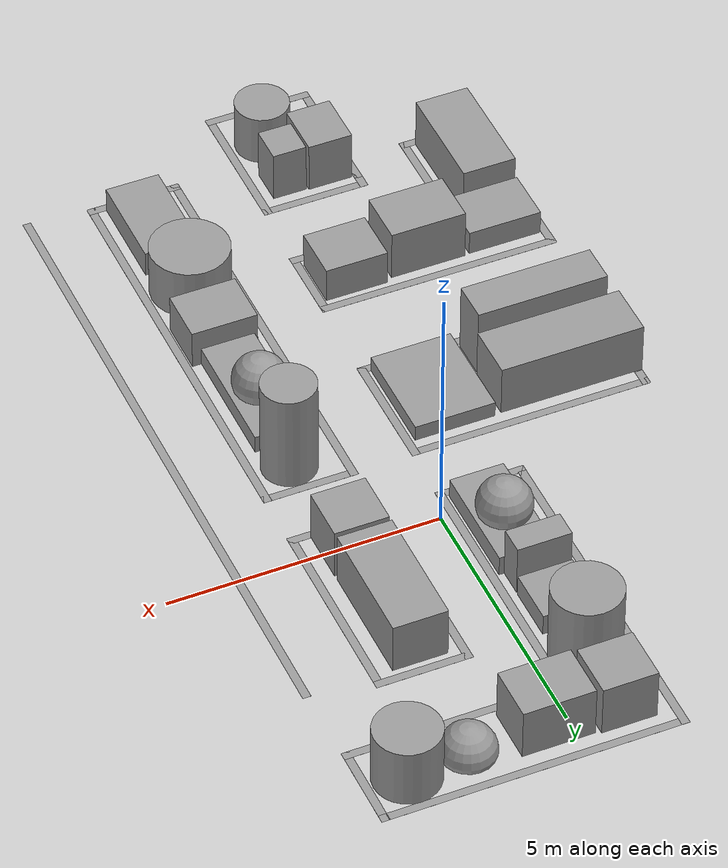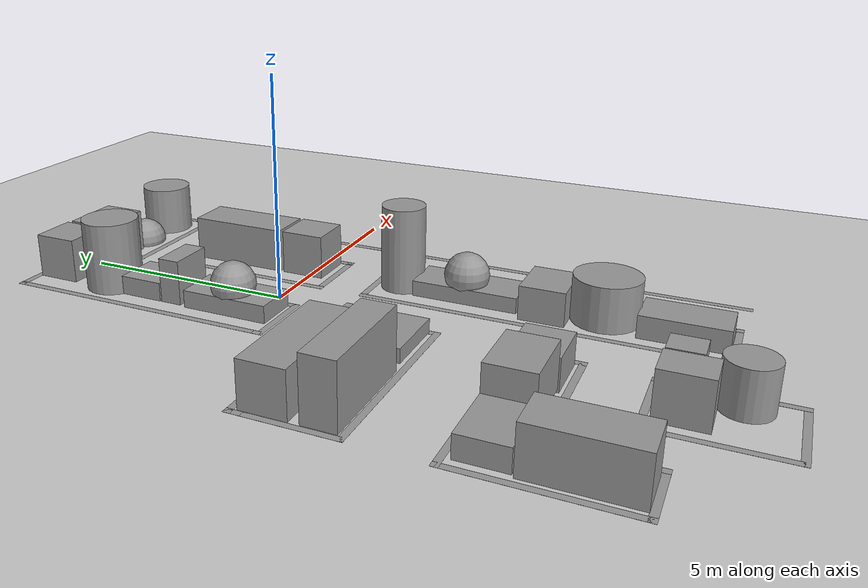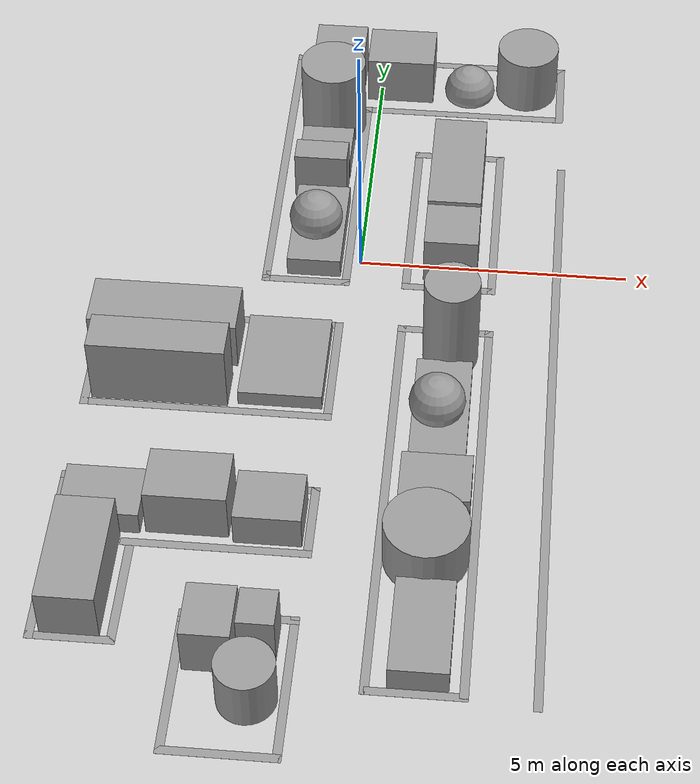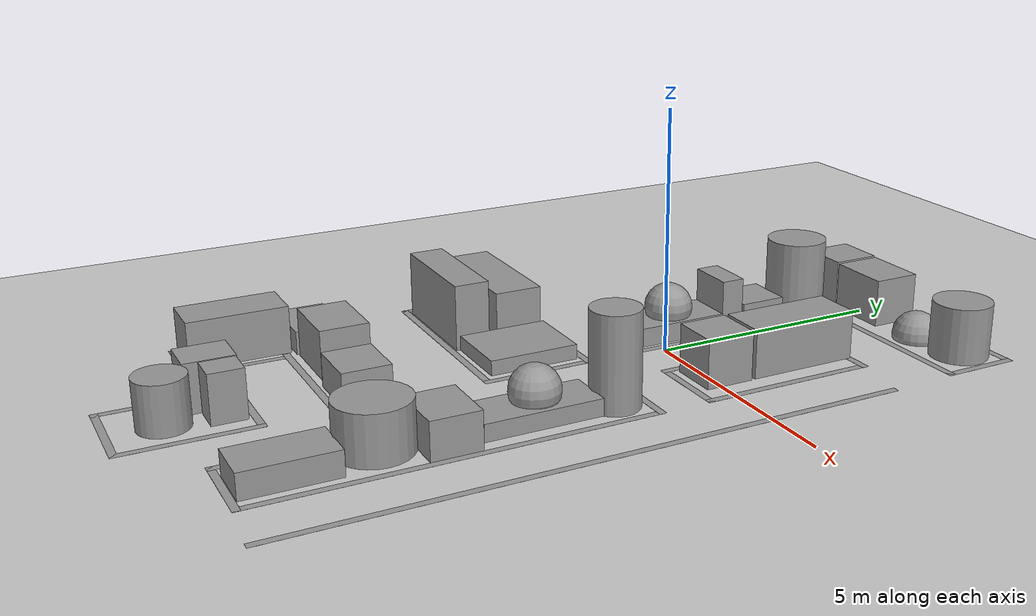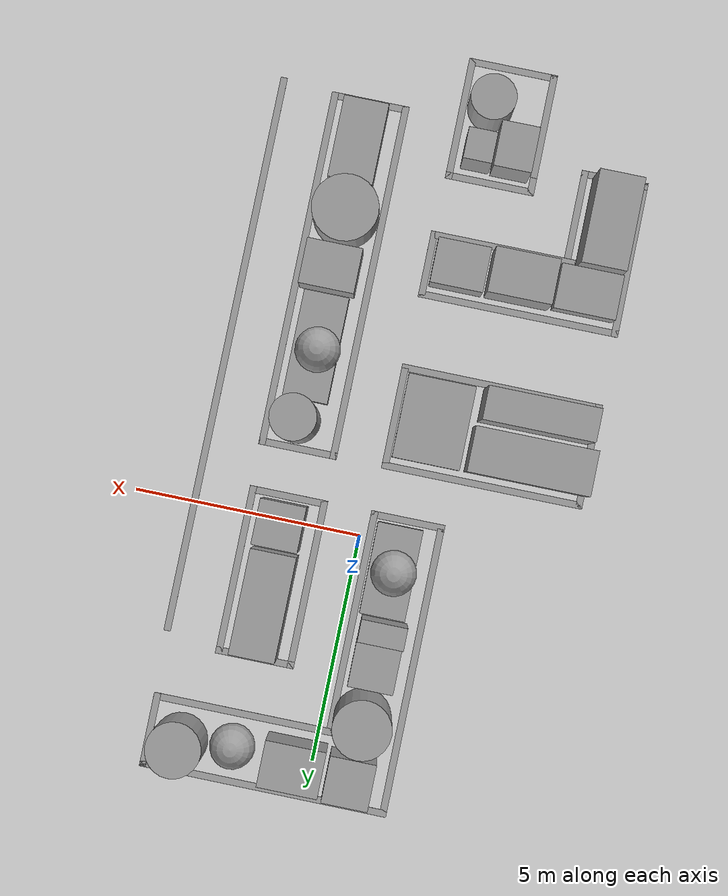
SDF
<sdf version="1.6">
 <world name="default">
  <scene><ambient>0.4 0.4 0.4 1</ambient><background>0.7 0.7 0.7 1</background><shadows>1</shadows></scene>
  <light name="sun" type="directional">
   <pose>0 0 10 0 -0 0</pose>
   <diffuse>0.8 0.8 0.8 1</diffuse>
   <specular>0.2 0.2 0.2 1</specular>
   <attenuation>
    <range>1000</range>
    <constant>0.9</constant>
    <linear>0.01</linear>
    <quadratic>0.001</quadratic>
   </attenuation>
   <direction>-0.5 0.1 -0.9</direction>
  </light>
  <model name="ground_plane">
   <static>1</static>
   <link name="link">
    <collision name="collision">
     <geometry><plane><normal>0 0 1</normal><size>100 100</size></plane></geometry>
     <surface>
      <contact><collide_bitmask>65535</collide_bitmask></contact>
      <friction><ode><mu>100</mu><mu2>50</mu2></ode></friction>
     </surface>
    </collision>
    <visual name="visual">
     <cast_shadows>0</cast_shadows>
     <geometry><plane><normal>0 0 1</normal><size>100 100</size></plane></geometry>
     <material>
      <script><uri>file://media/materials/scripts/gazebo.material</uri><name>Gazebo/Grey</name></script>
     </material>
    </visual>
   </link>
  </model>
  <model name="Untitled">
   <pose>-0.500001 -2.5 0 0 0 -1.57</pose>
   <link name="Wall_0">
    <collision name="Wall_0_Collision"><geometry><box><size>1.75 0.15 0.001</size></box></geometry></collision>
    <visual name="Wall_0_Visual">
     <geometry><box><size>1.75 0.15 0.001</size></box></geometry>
     <material>
      <script><uri>file://media/materials/scripts/gazebo.material</uri><name>Gazebo/Grey</name></script>
      <ambient>1 1 1 1</ambient>
     </material>
     <meta><layer>0</layer></meta>
    </visual>
    <pose>-1.96894 2.19842 0 0 -0 -1.5708</pose>
   </link>
   <link name="Wall_1">
    <collision name="Wall_1_Collision"><geometry><box><size>3.75 0.15 0.001</size></box></geometry></collision>
    <visual name="Wall_1_Visual">
     <geometry><box><size>3.75 0.15 0.001</size></box></geometry>
     <material>
      <script><uri>file://media/materials/scripts/gazebo.material</uri><name>Gazebo/Grey</name></script>
      <ambient>1 1 1 1</ambient>
     </material>
     <meta><layer>0</layer></meta>
    </visual>
    <pose>-3.76894 1.39842 0 0 -0 3.14159</pose>
   </link>
   <link name="Wall_10">
    <collision name="Wall_10_Collision"><geometry><box><size>1.75 0.15 0.001</size></box></geometry></collision>
    <visual name="Wall_10_Visual">
     <geometry><box><size>1.75 0.15 0.001</size></box></geometry>
     <material>
      <script><uri>file://media/materials/scripts/gazebo.material</uri><name>Gazebo/Grey</name></script>
      <ambient>1 1 1 1</ambient>
     </material>
     <meta><layer>0</layer></meta>
    </visual>
    <pose>6.95706 2.21142 0 0 -0 -1.5708</pose>
   </link>
   <link name="Wall_13">
    <collision name="Wall_13_Collision"><geometry><box><size>5 0.15 0.001</size></box></geometry></collision>
    <visual name="Wall_13_Visual">
     <geometry><box><size>5 0.15 0.001</size></box></geometry>
     <material>
      <script><uri>file://media/materials/scripts/gazebo.material</uri><name>Gazebo/Grey</name></script>
      <ambient>1 1 1 1</ambient>
     </material>
     <meta><layer>0</layer></meta>
    </visual>
    <pose>-4.39494 0.271425 0 0 -0 3.14159</pose>
   </link>
   <link name="Wall_16">
    <collision name="Wall_16_Collision"><geometry><box><size>4 0.15 0.001</size></box></geometry></collision>
    <visual name="Wall_16_Visual">
     <geometry><box><size>4 0.15 0.001</size></box></geometry>
     <material>
      <script><uri>file://media/materials/scripts/gazebo.material</uri><name>Gazebo/Grey</name></script>
      <ambient>1 1 1 1</ambient>
     </material>
     <meta><layer>0</layer></meta>
    </visual>
    <pose>-6.81994 2.19642 0 0 -0 1.5708</pose>
   </link>
   <link name="Wall_17">
    <collision name="Wall_17_Collision"><geometry><box><size>1.635 0.15 0.001</size></box></geometry></collision>
    <visual name="Wall_17_Visual">
     <geometry><box><size>1.635 0.15 0.001</size></box></geometry>
     <material>
      <script><uri>file://media/materials/scripts/gazebo.material</uri><name>Gazebo/Grey</name></script>
      <ambient>1 1 1 1</ambient>
     </material>
     <meta><layer>0</layer></meta>
    </visual>
    <pose>-7.56244 4.11992 0 0 -0 -3.13957</pose>
   </link>
   <link name="Wall_18">
    <collision name="Wall_18_Collision"><geometry><box><size>5.5 0.15 0.001</size></box></geometry></collision>
    <visual name="Wall_18_Visual">
     <geometry><box><size>5.5 0.15 0.001</size></box></geometry>
     <material>
      <script><uri>file://media/materials/scripts/gazebo.material</uri><name>Gazebo/Grey</name></script>
      <ambient>1 1 1 1</ambient>
     </material>
     <meta><layer>0</layer></meta>
    </visual>
    <pose>-8.30944 1.44342 0 0 -0 -1.57248</pose>
   </link>
   <link name="Wall_19">
    <collision name="Wall_19_Collision"><geometry><box><size>6.396 0.15 0.001</size></box></geometry></collision>
    <visual name="Wall_19_Visual">
     <geometry><box><size>6.396 0.15 0.001</size></box></geometry>
     <material>
      <script><uri>file://media/materials/scripts/gazebo.material</uri><name>Gazebo/Grey</name></script>
      <ambient>1 1 1 1</ambient>
     </material>
     <meta><layer>0</layer></meta>
    </visual>
    <pose>-5.19094 -1.23008 0 0 -0 0.00048</pose>
   </link>
   <link name="Wall_2">
    <collision name="Wall_2_Collision"><geometry><box><size>1.75 0.15 0.001</size></box></geometry></collision>
    <visual name="Wall_2_Visual">
     <geometry><box><size>1.75 0.15 0.001</size></box></geometry>
     <material>
      <script><uri>file://media/materials/scripts/gazebo.material</uri><name>Gazebo/Grey</name></script>
      <ambient>1 1 1 1</ambient>
     </material>
     <meta><layer>0</layer></meta>
    </visual>
    <pose>-5.56894 2.19842 0 0 -0 1.5708</pose>
   </link>
   <link name="Wall_20">
    <collision name="Wall_20_Collision"><geometry><box><size>0.25 0.15 0.001</size></box></geometry></collision>
    <visual name="Wall_20_Visual">
     <geometry><box><size>0.25 0.15 0.001</size></box></geometry>
     <material>
      <script><uri>file://media/materials/scripts/gazebo.material</uri><name>Gazebo/Grey</name></script>
      <ambient>1 1 1 1</ambient>
     </material>
     <meta><layer>0</layer></meta>
    </visual>
    <pose>-2.01794 -1.22857 0 0 -0 0</pose>
   </link>
   <link name="Wall_21">
    <collision name="Wall_21_Collision"><geometry><box><size>1.65 0.15 0.001</size></box></geometry></collision>
    <visual name="Wall_21_Visual">
     <geometry><box><size>1.65 0.15 0.001</size></box></geometry>
     <material>
      <script><uri>file://media/materials/scripts/gazebo.material</uri><name>Gazebo/Grey</name></script>
      <ambient>1 1 1 1</ambient>
     </material>
     <meta><layer>0</layer></meta>
    </visual>
    <pose>-1.96894 -0.478575 0 0 -0 1.57213</pose>
   </link>
   <link name="Wall_23">
    <collision name="Wall_23_Collision">
     <geometry><box><size>2.35234 0.15 0.001</size></box></geometry>
    </collision>
    <visual name="Wall_23_Visual">
     <geometry><box><size>2.35234 0.15 0.001</size></box></geometry>
     <material>
      <script><uri>file://media/materials/scripts/gazebo.material</uri><name>Gazebo/Grey</name></script>
      <ambient>1 1 1 1</ambient>
     </material>
     <meta><layer>0</layer></meta>
    </visual>
    <pose>0.233063 0.256924 0 0 -0 0.002271</pose>
   </link>
   <link name="Wall_24">
    <collision name="Wall_24_Collision">
     <geometry><box><size>4.50608 0.15 0.001</size></box></geometry>
    </collision>
    <visual name="Wall_24_Visual">
     <geometry><box><size>4.50608 0.15 0.001</size></box></geometry>
     <material>
      <script><uri>file://media/materials/scripts/gazebo.material</uri><name>Gazebo/Grey</name></script>
      <ambient>1 1 1 1</ambient>
     </material>
     <meta><layer>0</layer></meta>
    </visual>
    <pose>1.32956 -1.91858 0 0 -0 -1.57286</pose>
   </link>
   <link name="Wall_25">
    <collision name="Wall_25_Collision"><geometry><box><size>2 0.15 0.001</size></box></geometry></collision>
    <visual name="Wall_25_Visual">
     <geometry><box><size>2 0.15 0.001</size></box></geometry>
     <material>
      <script><uri>file://media/materials/scripts/gazebo.material</uri><name>Gazebo/Grey</name></script>
      <ambient>1 1 1 1</ambient>
     </material>
     <meta><layer>0</layer></meta>
    </visual>
    <pose>0.400063 -4.09657 0 0 -0 3.14159</pose>
   </link>
   <link name="Wall_28">
    <collision name="Wall_28_Collision"><geometry><box><size>4.5 0.15 0.001</size></box></geometry></collision>
    <visual name="Wall_28_Visual">
     <geometry><box><size>4.5 0.15 0.001</size></box></geometry>
     <material>
      <script><uri>file://media/materials/scripts/gazebo.material</uri><name>Gazebo/Grey</name></script>
      <ambient>1 1 1 1</ambient>
     </material>
     <meta><layer>0</layer></meta>
    </visual>
    <pose>-0.867937 -1.92057 0 0 -0 -1.5708</pose>
   </link>
   <link name="Wall_29">
    <collision name="Wall_29_Collision">
     <geometry><box><size>0.493001 0.15 0.001</size></box></geometry>
    </collision>
    <visual name="Wall_29_Visual">
     <geometry><box><size>0.493001 0.15 0.001</size></box></geometry>
     <material>
      <script><uri>file://media/materials/scripts/gazebo.material</uri><name>Gazebo/Grey</name></script>
      <ambient>1 1 1 1</ambient>
     </material>
     <meta><layer>0</layer></meta>
    </visual>
    <pose>-0.696437 -4.09608 0 0 -0 -0.002915</pose>
   </link>
   <link name="Wall_3">
    <collision name="Wall_3_Collision"><geometry><box><size>3.75 0.15 0.001</size></box></geometry></collision>
    <visual name="Wall_3_Visual">
     <geometry><box><size>3.75 0.15 0.001</size></box></geometry>
     <material>
      <script><uri>file://media/materials/scripts/gazebo.material</uri><name>Gazebo/Grey</name></script>
      <ambient>1 1 1 1</ambient>
     </material>
     <meta><layer>0</layer></meta>
    </visual>
    <pose>-3.76894 2.99842 0 0 -0 0</pose>
   </link>
   <link name="Wall_31">
    <collision name="Wall_31_Collision"><geometry><box><size>4.5 0.15 0.001</size></box></geometry></collision>
    <visual name="Wall_31_Visual">
     <geometry><box><size>4.5 0.15 0.001</size></box></geometry>
     <material>
      <script><uri>file://media/materials/scripts/gazebo.material</uri><name>Gazebo/Grey</name></script>
      <ambient>1 1 1 1</ambient>
     </material>
     <meta><layer>0</layer></meta>
    </visual>
    <pose>3.00606 -1.94657 0 0 -0 -1.5708</pose>
   </link>
   <link name="Wall_32">
    <collision name="Wall_32_Collision"><geometry><box><size>3.5 0.15 0.001</size></box></geometry></collision>
    <visual name="Wall_32_Visual">
     <geometry><box><size>3.5 0.15 0.001</size></box></geometry>
     <material>
      <script><uri>file://media/materials/scripts/gazebo.material</uri><name>Gazebo/Grey</name></script>
      <ambient>1 1 1 1</ambient>
     </material>
     <meta><layer>0</layer></meta>
    </visual>
    <pose>4.68106 -4.12157 0 0 -0 0</pose>
   </link>
   <link name="Wall_33">
    <collision name="Wall_33_Collision"><geometry><box><size>1.5 0.15 0.001</size></box></geometry></collision>
    <visual name="Wall_33_Visual">
     <geometry><box><size>1.5 0.15 0.001</size></box></geometry>
     <material>
      <script><uri>file://media/materials/scripts/gazebo.material</uri><name>Gazebo/Grey</name></script>
      <ambient>1 1 1 1</ambient>
     </material>
     <meta><layer>0</layer></meta>
    </visual>
    <pose>6.35606 -3.44658 0 0 -0 1.5708</pose>
   </link>
   <link name="Wall_34">
    <collision name="Wall_34_Collision"><geometry><box><size>2 0.15 0.001</size></box></geometry></collision>
    <visual name="Wall_34_Visual">
     <geometry><box><size>2 0.15 0.001</size></box></geometry>
     <material>
      <script><uri>file://media/materials/scripts/gazebo.material</uri><name>Gazebo/Grey</name></script>
      <ambient>1 1 1 1</ambient>
     </material>
     <meta><layer>0</layer></meta>
    </visual>
    <pose>5.43106 -2.77158 0 0 -0 3.14159</pose>
   </link>
   <link name="Wall_39">
    <collision name="Wall_39_Collision"><geometry><box><size>1.5 0.15 0.001</size></box></geometry></collision>
    <visual name="Wall_39_Visual">
     <geometry><box><size>1.5 0.15 0.001</size></box></geometry>
     <material>
      <script><uri>file://media/materials/scripts/gazebo.material</uri><name>Gazebo/Grey</name></script>
      <ambient>1 1 1 1</ambient>
     </material>
     <meta><layer>0</layer></meta>
    </visual>
    <pose>3.68106 0.228424 0 0 -0 0</pose>
   </link>
   <link name="Wall_40">
    <collision name="Wall_40_Collision"><geometry><box><size>3.25 0.15 0.001</size></box></geometry></collision>
    <visual name="Wall_40_Visual">
     <geometry><box><size>3.25 0.15 0.001</size></box></geometry>
     <material>
      <script><uri>file://media/materials/scripts/gazebo.material</uri><name>Gazebo/Grey</name></script>
      <ambient>1 1 1 1</ambient>
     </material>
     <meta><layer>0</layer></meta>
    </visual>
    <pose>4.35606 -1.32157 0 0 -0 -1.5708</pose>
   </link>
   <link name="Wall_42">
    <collision name="Wall_42_Collision"><geometry><box><size>2.75 0.15 0.001</size></box></geometry></collision>
    <visual name="Wall_42_Visual">
     <geometry><box><size>2.75 0.15 0.001</size></box></geometry>
     <material>
      <script><uri>file://media/materials/scripts/gazebo.material</uri><name>Gazebo/Grey</name></script>
      <ambient>1 1 1 1</ambient>
     </material>
     <meta><layer>0</layer></meta>
    </visual>
    <pose>7.01406 0.172425 0 0 -0 0</pose>
   </link>
   <link name="Wall_43">
    <collision name="Wall_43_Collision"><geometry><box><size>2 0.15 0.001</size></box></geometry></collision>
    <visual name="Wall_43_Visual">
     <geometry><box><size>2 0.15 0.001</size></box></geometry>
     <material>
      <script><uri>file://media/materials/scripts/gazebo.material</uri><name>Gazebo/Grey</name></script>
      <ambient>1 1 1 1</ambient>
     </material>
     <meta><layer>0</layer></meta>
    </visual>
    <pose>8.31406 -0.752576 0 0 -0 -1.5708</pose>
   </link>
   <link name="Wall_44">
    <collision name="Wall_44_Collision"><geometry><box><size>2.5 0.15 0.001</size></box></geometry></collision>
    <visual name="Wall_44_Visual">
     <geometry><box><size>2.5 0.15 0.001</size></box></geometry>
     <material>
      <script><uri>file://media/materials/scripts/gazebo.material</uri><name>Gazebo/Grey</name></script>
      <ambient>1 1 1 1</ambient>
     </material>
     <meta><layer>0</layer></meta>
    </visual>
    <pose>7.13906 -1.67758 0 0 -0 3.14159</pose>
   </link>
   <link name="Wall_47">
    <collision name="Wall_47_Collision"><geometry><box><size>2 0.15 0.001</size></box></geometry></collision>
    <visual name="Wall_47_Visual">
     <geometry><box><size>2 0.15 0.001</size></box></geometry>
     <material>
      <script><uri>file://media/materials/scripts/gazebo.material</uri><name>Gazebo/Grey</name></script>
      <ambient>1 1 1 1</ambient>
     </material>
     <meta><layer>0</layer></meta>
    </visual>
    <pose>5.71406 -0.752576 0 0 -0 -1.5708</pose>
   </link>
   <link name="Wall_48">
    <collision name="Wall_48_Collision"><geometry><box><size>0.4 0.15 0.001</size></box></geometry></collision>
    <visual name="Wall_48_Visual">
     <geometry><box><size>0.4 0.15 0.001</size></box></geometry>
     <material>
      <script><uri>file://media/materials/scripts/gazebo.material</uri><name>Gazebo/Grey</name></script>
      <ambient>1 1 1 1</ambient>
     </material>
     <meta><layer>0</layer></meta>
    </visual>
    <pose>5.83906 -1.67758 0 0 -0 0</pose>
   </link>
   <link name="Wall_6">
    <collision name="Wall_6_Collision"><geometry><box><size>8 0.15 0.001</size></box></geometry></collision>
    <visual name="Wall_6_Visual">
     <geometry><box><size>8 0.15 0.001</size></box></geometry>
     <material>
      <script><uri>file://media/materials/scripts/gazebo.material</uri><name>Gazebo/Grey</name></script>
      <ambient>1 1 1 1</ambient>
     </material>
     <meta><layer>0</layer></meta>
    </visual>
    <pose>3.03206 1.41142 0 0 -0 0</pose>
   </link>
   <link name="Wall_8">
    <collision name="Wall_8_Collision"><geometry><box><size>1.75 0.15 0.001</size></box></geometry></collision>
    <visual name="Wall_8_Visual">
     <geometry><box><size>1.75 0.15 0.001</size></box></geometry>
     <material>
      <script><uri>file://media/materials/scripts/gazebo.material</uri><name>Gazebo/Grey</name></script>
      <ambient>1 1 1 1</ambient>
     </material>
     <meta><layer>0</layer></meta>
    </visual>
    <pose>-0.892937 2.21142 0 0 -0 1.5708</pose>
   </link>
   <link name="Wall_9">
    <collision name="Wall_9_Collision"><geometry><box><size>8 0.15 0.001</size></box></geometry></collision>
    <visual name="Wall_9_Visual">
     <geometry><box><size>8 0.15 0.001</size></box></geometry>
     <material>
      <script><uri>file://media/materials/scripts/gazebo.material</uri><name>Gazebo/Grey</name></script>
      <ambient>1 1 1 1</ambient>
     </material>
     <meta><layer>0</layer></meta>
    </visual>
    <pose>3.03206 3.01142 0 0 -0 0</pose>
   </link>
   <static>1</static>
  </model>
  <physics name="default_physics" default="0" type="ode">
   <real_time_update_rate>1000</real_time_update_rate>
   <max_step_size>0.001</max_step_size>
   <real_time_factor>1</real_time_factor>
   <ode>
    <solver>
     <type>quick</type>
     <iters>150</iters>
     <precon_iters>0</precon_iters>
     <sor>1.4</sor>
     <use_dynamic_moi_rescaling>1</use_dynamic_moi_rescaling>
    </solver>
    <constraints>
     <cfm>1e-05</cfm>
     <erp>0.2</erp>
     <contact_max_correcting_vel>2000</contact_max_correcting_vel>
     <contact_surface_layer>0.001</contact_surface_layer>
    </constraints>
   </ode>
  </physics>
  <gravity>0 0 -9.8</gravity>
  <magnetic_field>6e-06 2.3e-05 -4.2e-05</magnetic_field>
  <atmosphere type="adiabatic"/>
  <audio><device>default</device></audio>
  <spherical_coordinates>
   <surface_model>EARTH_WGS84</surface_model>
   <latitude_deg>0</latitude_deg>
   <longitude_deg>0</longitude_deg>
   <elevation>0</elevation>
   <heading_deg>0</heading_deg>
  </spherical_coordinates>
  <model name="buildings">
   <link name="link_0">
    <inertial>
     <mass>2.05987</mass>
     <inertia><ixx>0.9</ixx><ixy>0</ixy><ixz>0</ixz><iyy>0.343312</iyy><iyz>0</iyz><izz>0.9</izz></inertia>
    </inertial>
    <pose>-3.65731 -5.49674 0.040889 0 -0 0</pose>
    <visual name="visual">
     <geometry><box><size>1 2.05987 1</size></box></geometry>
     <material>
      <lighting>1</lighting>
      <script><uri>file://media/materials/scripts/gazebo.material</uri><name>Gazebo/Grey</name></script>
     </material>
    </visual>
    <collision name="collision">
     <geometry><box><size>1 2.05987 1</size></box></geometry>
     <surface>
      <friction>
       <ode><mu>1</mu><mu2>1</mu2><fdir1>0 0 0</fdir1><slip1>0</slip1><slip2>0</slip2></ode>
       <torsional>
        <coefficient>1</coefficient>
        <patch_radius>0</patch_radius>
        <surface_radius>0</surface_radius>
        <use_patch_radius>1</use_patch_radius>
        <ode><slip>0</slip></ode>
       </torsional>
      </friction>
      <bounce><restitution_coefficient>0</restitution_coefficient><threshold>1e+06</threshold></bounce>
      <contact>
       <collide_without_contact>0</collide_without_contact>
       <collide_without_contact_bitmask>1</collide_without_contact_bitmask>
       <collide_bitmask>1</collide_bitmask>
       <ode>
        <soft_cfm>0</soft_cfm>
        <soft_erp>0.2</soft_erp>
        <kp>1e+13</kp>
        <kd>1</kd>
        <max_vel>0.01</max_vel>
        <min_depth>0</min_depth>
       </ode>
       <bullet>
        <split_impulse>1</split_impulse>
        <split_impulse_penetration_threshold>-0.01</split_impulse_penetration_threshold>
        <soft_cfm>0</soft_cfm>
        <soft_erp>0.2</soft_erp>
        <kp>1e+13</kp>
        <kd>1</kd>
       </bullet>
      </contact>
     </surface>
    </collision>
   </link>
   <link name="link_1">
    <inertial>
     <mass>0.657597</mass>
     <inertia>
      <ixx>0.067355</ixx>
      <ixy>0</ixy>
      <ixz>0</ixz>
      <iyy>0.115971</iyy>
      <iyz>0</iyz>
      <izz>0.158216</izz>
     </inertia>
    </inertial>
    <pose>-3.50191 -3.95273 -0.145196 0 -0 0</pose>
    <visual name="visual">
     <geometry><box><size>1.37374 1 0.478656</size></box></geometry>
     <material>
      <lighting>1</lighting>
      <script><uri>file://media/materials/scripts/gazebo.material</uri><name>Gazebo/Grey</name></script>
     </material>
    </visual>
    <collision name="collision">
     <geometry><box><size>1.37374 1 0.478656</size></box></geometry>
     <surface>
      <friction>
       <ode><mu>1</mu><mu2>1</mu2><fdir1>0 0 0</fdir1><slip1>0</slip1><slip2>0</slip2></ode>
       <torsional>
        <coefficient>1</coefficient>
        <patch_radius>0</patch_radius>
        <surface_radius>0</surface_radius>
        <use_patch_radius>1</use_patch_radius>
        <ode><slip>0</slip></ode>
       </torsional>
      </friction>
      <bounce><restitution_coefficient>0</restitution_coefficient><threshold>1e+06</threshold></bounce>
      <contact>
       <collide_without_contact>0</collide_without_contact>
       <collide_without_contact_bitmask>1</collide_without_contact_bitmask>
       <collide_bitmask>1</collide_bitmask>
       <ode>
        <soft_cfm>0</soft_cfm>
        <soft_erp>0.2</soft_erp>
        <kp>1e+13</kp>
        <kd>1</kd>
        <max_vel>0.01</max_vel>
        <min_depth>0</min_depth>
       </ode>
       <bullet>
        <split_impulse>1</split_impulse>
        <split_impulse_penetration_threshold>-0.01</split_impulse_penetration_threshold>
        <soft_cfm>0</soft_cfm>
        <soft_erp>0.2</soft_erp>
        <kp>1e+13</kp>
        <kd>1</kd>
       </bullet>
      </contact>
     </surface>
    </collision>
   </link>
   <link name="link_10">
    <inertial>
     <mass>1.22906</mass>
     <inertia>
      <ixx>0.204843</ixx>
      <ixy>0</ixy>
      <ixz>0</ixz>
      <iyy>0.257137</iyy>
      <iyz>0</iyz>
      <izz>0.257137</izz>
     </inertia>
    </inertial>
    <pose>2.09374 -3.3423 -0.211317 0 -0 0</pose>
    <visual name="visual">
     <geometry><box><size>1.22906 1 1</size></box></geometry>
     <material>
      <lighting>1</lighting>
      <script><uri>file://media/materials/scripts/gazebo.material</uri><name>Gazebo/Grey</name></script>
     </material>
    </visual>
    <collision name="collision">
     <geometry><box><size>1.22906 1 1</size></box></geometry>
     <surface>
      <friction>
       <ode><mu>1</mu><mu2>1</mu2><fdir1>0 0 0</fdir1><slip1>0</slip1><slip2>0</slip2></ode>
       <torsional>
        <coefficient>1</coefficient>
        <patch_radius>0</patch_radius>
        <surface_radius>0</surface_radius>
        <use_patch_radius>1</use_patch_radius>
        <ode><slip>0</slip></ode>
       </torsional>
      </friction>
      <bounce><restitution_coefficient>0</restitution_coefficient><threshold>1e+06</threshold></bounce>
      <contact>
       <collide_without_contact>0</collide_without_contact>
       <collide_without_contact_bitmask>1</collide_without_contact_bitmask>
       <collide_bitmask>1</collide_bitmask>
       <ode>
        <soft_cfm>0</soft_cfm>
        <soft_erp>0.2</soft_erp>
        <kp>1e+13</kp>
        <kd>1</kd>
        <max_vel>0.01</max_vel>
        <min_depth>0</min_depth>
       </ode>
       <bullet>
        <split_impulse>1</split_impulse>
        <split_impulse_penetration_threshold>-0.01</split_impulse_penetration_threshold>
        <soft_cfm>0</soft_cfm>
        <soft_erp>0.2</soft_erp>
        <kp>1e+13</kp>
        <kd>1</kd>
       </bullet>
      </contact>
     </surface>
    </collision>
   </link>
   <link name="link_11">
    <inertial>
     <mass>2.12736</mass>
     <inertia>
      <ixx>0.460131</ixx>
      <ixy>0</ixy>
      <ixz>0</ixz>
      <iyy>0.460131</iyy>
      <iyz>0</iyz>
      <izz>0.565703</izz>
     </inertia>
    </inertial>
    <pose>2.02003 -4.57597 0.124873 0 -0 0</pose>
    <visual name="visual">
     <geometry><cylinder><radius>0.729271</radius><length>1</length></cylinder></geometry>
     <material>
      <lighting>1</lighting>
      <script><uri>file://media/materials/scripts/gazebo.material</uri><name>Gazebo/Grey</name></script>
     </material>
    </visual>
    <collision name="collision">
     <geometry><cylinder><radius>0.729271</radius><length>1</length></cylinder></geometry>
     <surface>
      <friction>
       <ode><mu>1</mu><mu2>1</mu2><fdir1>0 0 0</fdir1><slip1>0</slip1><slip2>0</slip2></ode>
       <torsional>
        <coefficient>1</coefficient>
        <patch_radius>0</patch_radius>
        <surface_radius>0</surface_radius>
        <use_patch_radius>1</use_patch_radius>
        <ode><slip>0</slip></ode>
       </torsional>
      </friction>
      <bounce><restitution_coefficient>0</restitution_coefficient><threshold>1e+06</threshold></bounce>
      <contact>
       <collide_without_contact>0</collide_without_contact>
       <collide_without_contact_bitmask>1</collide_without_contact_bitmask>
       <collide_bitmask>1</collide_bitmask>
       <ode>
        <soft_cfm>0</soft_cfm>
        <soft_erp>0.2</soft_erp>
        <kp>1e+13</kp>
        <kd>1</kd>
        <max_vel>0.01</max_vel>
        <min_depth>0</min_depth>
       </ode>
       <bullet>
        <split_impulse>1</split_impulse>
        <split_impulse_penetration_threshold>-0.01</split_impulse_penetration_threshold>
        <soft_cfm>0</soft_cfm>
        <soft_erp>0.2</soft_erp>
        <kp>1e+13</kp>
        <kd>1</kd>
       </bullet>
      </contact>
     </surface>
    </collision>
   </link>
   <link name="link_12">
    <inertial>
     <mass>0.922792</mass>
     <inertia>
      <ixx>0.275517</ixx>
      <ixy>0</ixy>
      <ixz>0</ixz>
      <iyy>0.0965958</iyy>
      <iyz>0</iyz>
      <izz>0.33272</izz>
     </inertia>
    </inertial>
    <pose>2.07608 -6.19758 -0.205607 0 -0 0</pose>
    <visual name="visual">
     <geometry><box><size>1 1.82392 0.506096</size></box></geometry>
     <material>
      <lighting>1</lighting>
      <script><uri>file://media/materials/scripts/gazebo.material</uri><name>Gazebo/Grey</name></script>
     </material>
    </visual>
    <collision name="collision">
     <geometry><box><size>1 1.82392 0.506096</size></box></geometry>
     <surface>
      <friction>
       <ode><mu>1</mu><mu2>1</mu2><fdir1>0 0 0</fdir1><slip1>0</slip1><slip2>0</slip2></ode>
       <torsional>
        <coefficient>1</coefficient>
        <patch_radius>0</patch_radius>
        <surface_radius>0</surface_radius>
        <use_patch_radius>1</use_patch_radius>
        <ode><slip>0</slip></ode>
       </torsional>
      </friction>
      <bounce><restitution_coefficient>0</restitution_coefficient><threshold>1e+06</threshold></bounce>
      <contact>
       <collide_without_contact>0</collide_without_contact>
       <collide_without_contact_bitmask>1</collide_without_contact_bitmask>
       <collide_bitmask>1</collide_bitmask>
       <ode>
        <soft_cfm>0</soft_cfm>
        <soft_erp>0.2</soft_erp>
        <kp>1e+13</kp>
        <kd>1</kd>
        <max_vel>0.01</max_vel>
        <min_depth>0</min_depth>
       </ode>
       <bullet>
        <split_impulse>1</split_impulse>
        <split_impulse_penetration_threshold>-0.01</split_impulse_penetration_threshold>
        <soft_cfm>0</soft_cfm>
        <soft_erp>0.2</soft_erp>
        <kp>1e+13</kp>
        <kd>1</kd>
       </bullet>
      </contact>
     </surface>
    </collision>
   </link>
   <link name="link_13">
    <inertial>
     <mass>0.867163</mass>
     <inertia>
      <ixx>0.259684</ixx>
      <ixy>0</ixy>
      <ixz>0</ixz>
      <iyy>0.169359</iyy>
      <iyz>0</iyz>
      <izz>0.415215</izz>
     </inertia>
    </inertial>
    <pose>-0.790765 -0.511354 -0.245848 0 -0 0</pose>
    <visual name="visual">
     <geometry><box><size>1.49932 1.87027 0.309309</size></box></geometry>
     <material>
      <lighting>1</lighting>
      <script><uri>file://media/materials/scripts/gazebo.material</uri><name>Gazebo/Grey</name></script>
     </material>
    </visual>
    <collision name="collision">
     <geometry><box><size>1.49932 1.87027 0.309309</size></box></geometry>
     <surface>
      <friction>
       <ode><mu>1</mu><mu2>1</mu2><fdir1>0 0 0</fdir1><slip1>0</slip1><slip2>0</slip2></ode>
       <torsional>
        <coefficient>1</coefficient>
        <patch_radius>0</patch_radius>
        <surface_radius>0</surface_radius>
        <use_patch_radius>1</use_patch_radius>
        <ode><slip>0</slip></ode>
       </torsional>
      </friction>
      <bounce><restitution_coefficient>0</restitution_coefficient><threshold>1e+06</threshold></bounce>
      <contact>
       <collide_without_contact>0</collide_without_contact>
       <collide_without_contact_bitmask>1</collide_without_contact_bitmask>
       <collide_bitmask>1</collide_bitmask>
       <ode>
        <soft_cfm>0</soft_cfm>
        <soft_erp>0.2</soft_erp>
        <kp>1e+13</kp>
        <kd>1</kd>
        <max_vel>0.01</max_vel>
        <min_depth>0</min_depth>
       </ode>
       <bullet>
        <split_impulse>1</split_impulse>
        <split_impulse_penetration_threshold>-0.01</split_impulse_penetration_threshold>
        <soft_cfm>0</soft_cfm>
        <soft_erp>0.2</soft_erp>
        <kp>1e+13</kp>
        <kd>1</kd>
       </bullet>
      </contact>
     </surface>
    </collision>
   </link>
   <link name="link_14">
    <inertial>
     <mass>2.79733</mass>
     <inertia><ixx>0.692471</ixx><ixy>0</ixy><ixz>0</ixz><iyy>1.95677</iyy><iyz>0</iyz><izz>1.51593</izz></inertia>
    </inertial>
    <pose>-2.95025 -1.08442 0.124873 0 -0 0</pose>
    <visual name="visual">
     <geometry><box><size>2.44199 0.734656 1.55912</size></box></geometry>
     <material>
      <lighting>1</lighting>
      <script><uri>file://media/materials/scripts/gazebo.material</uri><name>Gazebo/Grey</name></script>
     </material>
    </visual>
    <collision name="collision">
     <geometry><box><size>2.44199 0.734656 1.55912</size></box></geometry>
     <surface>
      <friction>
       <ode><mu>1</mu><mu2>1</mu2><fdir1>0 0 0</fdir1><slip1>0</slip1><slip2>0</slip2></ode>
       <torsional>
        <coefficient>1</coefficient>
        <patch_radius>0</patch_radius>
        <surface_radius>0</surface_radius>
        <use_patch_radius>1</use_patch_radius>
        <ode><slip>0</slip></ode>
       </torsional>
      </friction>
      <bounce><restitution_coefficient>0</restitution_coefficient><threshold>1e+06</threshold></bounce>
      <contact>
       <collide_without_contact>0</collide_without_contact>
       <collide_without_contact_bitmask>1</collide_without_contact_bitmask>
       <collide_bitmask>1</collide_bitmask>
       <ode>
        <soft_cfm>0</soft_cfm>
        <soft_erp>0.2</soft_erp>
        <kp>1e+13</kp>
        <kd>1</kd>
        <max_vel>0.01</max_vel>
        <min_depth>0</min_depth>
       </ode>
       <bullet>
        <split_impulse>1</split_impulse>
        <split_impulse_penetration_threshold>-0.01</split_impulse_penetration_threshold>
        <soft_cfm>0</soft_cfm>
        <soft_erp>0.2</soft_erp>
        <kp>1e+13</kp>
        <kd>1</kd>
       </bullet>
      </contact>
     </surface>
    </collision>
   </link>
   <link name="link_15">
    <inertial>
     <mass>0.795978</mass>
     <inertia>
      <ixx>0.279163</ixx>
      <ixy>0</ixy>
      <ixz>0</ixz>
      <iyy>0.0767026</iyy>
      <iyz>0</iyz>
      <izz>0.335124</izz>
     </inertia>
    </inertial>
    <pose>-0.533513 2.86402 -0.241441 0 -0 0</pose>
    <visual name="visual">
     <geometry><box><size>1 2.01302 0.395414</size></box></geometry>
     <material>
      <lighting>1</lighting>
      <script><uri>file://media/materials/scripts/gazebo.material</uri><name>Gazebo/Grey</name></script>
     </material>
    </visual>
    <collision name="collision">
     <geometry><box><size>1 2.01302 0.395414</size></box></geometry>
     <surface>
      <friction>
       <ode><mu>1</mu><mu2>1</mu2><fdir1>0 0 0</fdir1><slip1>0</slip1><slip2>0</slip2></ode>
       <torsional>
        <coefficient>1</coefficient>
        <patch_radius>0</patch_radius>
        <surface_radius>0</surface_radius>
        <use_patch_radius>1</use_patch_radius>
        <ode><slip>0</slip></ode>
       </torsional>
      </friction>
      <bounce><restitution_coefficient>0</restitution_coefficient><threshold>1e+06</threshold></bounce>
      <contact>
       <collide_without_contact>0</collide_without_contact>
       <collide_without_contact_bitmask>1</collide_without_contact_bitmask>
       <collide_bitmask>1</collide_bitmask>
       <ode>
        <soft_cfm>0</soft_cfm>
        <soft_erp>0.2</soft_erp>
        <kp>1e+13</kp>
        <kd>1</kd>
        <max_vel>0.01</max_vel>
        <min_depth>0</min_depth>
       </ode>
       <bullet>
        <split_impulse>1</split_impulse>
        <split_impulse_penetration_threshold>-0.01</split_impulse_penetration_threshold>
        <soft_cfm>0</soft_cfm>
        <soft_erp>0.2</soft_erp>
        <kp>1e+13</kp>
        <kd>1</kd>
       </bullet>
      </contact>
     </surface>
    </collision>
   </link>
   <link name="link_16">
    <inertial>
     <mass>0.490895</mass>
     <inertia>
      <ixx>0.0507658</ixx>
      <ixy>0</ixy>
      <ixz>0</ixz>
      <iyy>0.0818158</iyy>
      <iyz>0</iyz>
      <izz>0.0507658</izz>
     </inertia>
    </inertial>
    <pose>-0.602063 4.16739 0.124873 0 -0 0</pose>
    <visual name="visual">
     <geometry><box><size>1 0.490896 1</size></box></geometry>
     <material>
      <lighting>1</lighting>
      <script><uri>file://media/materials/scripts/gazebo.material</uri><name>Gazebo/Grey</name></script>
     </material>
    </visual>
    <collision name="collision">
     <geometry><box><size>1 0.490896 1</size></box></geometry>
     <surface>
      <friction>
       <ode><mu>1</mu><mu2>1</mu2><fdir1>0 0 0</fdir1><slip1>0</slip1><slip2>0</slip2></ode>
       <torsional>
        <coefficient>1</coefficient>
        <patch_radius>0</patch_radius>
        <surface_radius>0</surface_radius>
        <use_patch_radius>1</use_patch_radius>
        <ode><slip>0</slip></ode>
       </torsional>
      </friction>
      <bounce><restitution_coefficient>0</restitution_coefficient><threshold>1e+06</threshold></bounce>
      <contact>
       <collide_without_contact>0</collide_without_contact>
       <collide_without_contact_bitmask>1</collide_without_contact_bitmask>
       <collide_bitmask>1</collide_bitmask>
       <ode>
        <soft_cfm>0</soft_cfm>
        <soft_erp>0.2</soft_erp>
        <kp>1e+13</kp>
        <kd>1</kd>
        <max_vel>0.01</max_vel>
        <min_depth>0</min_depth>
       </ode>
       <bullet>
        <split_impulse>1</split_impulse>
        <split_impulse_penetration_threshold>-0.01</split_impulse_penetration_threshold>
        <soft_cfm>0</soft_cfm>
        <soft_erp>0.2</soft_erp>
        <kp>1e+13</kp>
        <kd>1</kd>
       </bullet>
      </contact>
     </surface>
    </collision>
   </link>
   <link name="link_17">
    <inertial>
     <mass>0.420034</mass>
     <inertia>
      <ixx>0.0411783</ixx>
      <ixy>0</ixy>
      <ixz>0</ixz>
      <iyy>0.0411783</iyy>
      <iyz>0</iyz>
      <izz>0.0700057</izz>
     </inertia>
    </inertial>
    <pose>-0.598739 4.95645 -0.169955 0 -0 0</pose>
    <visual name="visual">
     <geometry><box><size>1 1 0.420032</size></box></geometry>
     <material>
      <lighting>1</lighting>
      <script><uri>file://media/materials/scripts/gazebo.material</uri><name>Gazebo/Grey</name></script>
     </material>
    </visual>
    <collision name="collision">
     <geometry><box><size>1 1 0.420032</size></box></geometry>
     <surface>
      <friction>
       <ode><mu>1</mu><mu2>1</mu2><fdir1>0 0 0</fdir1><slip1>0</slip1><slip2>0</slip2></ode>
       <torsional>
        <coefficient>1</coefficient>
        <patch_radius>0</patch_radius>
        <surface_radius>0</surface_radius>
        <use_patch_radius>1</use_patch_radius>
        <ode><slip>0</slip></ode>
       </torsional>
      </friction>
      <bounce><restitution_coefficient>0</restitution_coefficient><threshold>1e+06</threshold></bounce>
      <contact>
       <collide_without_contact>0</collide_without_contact>
       <collide_without_contact_bitmask>1</collide_without_contact_bitmask>
       <collide_bitmask>1</collide_bitmask>
       <ode>
        <soft_cfm>0</soft_cfm>
        <soft_erp>0.2</soft_erp>
        <kp>1e+13</kp>
        <kd>1</kd>
        <max_vel>0.01</max_vel>
        <min_depth>0</min_depth>
       </ode>
       <bullet>
        <split_impulse>1</split_impulse>
        <split_impulse_penetration_threshold>-0.01</split_impulse_penetration_threshold>
        <soft_cfm>0</soft_cfm>
        <soft_erp>0.2</soft_erp>
        <kp>1e+13</kp>
        <kd>1</kd>
       </bullet>
      </contact>
     </surface>
    </collision>
   </link>
   <link name="link_18">
    <inertial>
     <mass>3.4661</mass>
     <inertia><ixx>1.72412</ixx><ixy>0</ixy><ixz>0</ixz><iyy>1.72412</iyy><iyz>0</iyz><izz>0.68687</izz></inertia>
    </inertial>
    <pose>-0.565649 6.11246 0.056395 0 -0 0</pose>
    <visual name="visual">
     <geometry><cylinder><radius>0.629552</radius><length>2.18634</length></cylinder></geometry>
     <material>
      <lighting>1</lighting>
      <script><uri>file://media/materials/scripts/gazebo.material</uri><name>Gazebo/Grey</name></script>
     </material>
    </visual>
    <collision name="collision">
     <geometry><cylinder><radius>0.629552</radius><length>2.18634</length></cylinder></geometry>
     <surface>
      <friction>
       <ode><mu>1</mu><mu2>1</mu2><fdir1>0 0 0</fdir1><slip1>0</slip1><slip2>0</slip2></ode>
       <torsional>
        <coefficient>1</coefficient>
        <patch_radius>0</patch_radius>
        <surface_radius>0</surface_radius>
        <use_patch_radius>1</use_patch_radius>
        <ode><slip>0</slip></ode>
       </torsional>
      </friction>
      <bounce><restitution_coefficient>0</restitution_coefficient><threshold>1e+06</threshold></bounce>
      <contact>
       <collide_without_contact>0</collide_without_contact>
       <collide_without_contact_bitmask>1</collide_without_contact_bitmask>
       <collide_bitmask>1</collide_bitmask>
       <ode>
        <soft_cfm>0</soft_cfm>
        <soft_erp>0.2</soft_erp>
        <kp>1e+13</kp>
        <kd>1</kd>
        <max_vel>0.01</max_vel>
        <min_depth>0</min_depth>
       </ode>
       <bullet>
        <split_impulse>1</split_impulse>
        <split_impulse_penetration_threshold>-0.01</split_impulse_penetration_threshold>
        <soft_cfm>0</soft_cfm>
        <soft_erp>0.2</soft_erp>
        <kp>1e+13</kp>
        <kd>1</kd>
       </bullet>
      </contact>
     </surface>
    </collision>
   </link>
   <link name="link_19">
    <inertial>
     <mass>1</mass>
     <inertia>
      <ixx>0.166667</ixx>
      <ixy>0</ixy>
      <ixz>0</ixz>
      <iyy>0.166667</iyy>
      <iyz>0</iyz>
      <izz>0.166667</izz>
     </inertia>
    </inertial>
    <pose>-0.537522 7.36063 0.124873 0 -0 0</pose>
    <visual name="visual">
     <geometry><box><size>1 1 1</size></box></geometry>
     <material>
      <lighting>1</lighting>
      <script><uri>file://media/materials/scripts/gazebo.material</uri><name>Gazebo/Grey</name></script>
     </material>
    </visual>
    <collision name="collision">
     <geometry><box><size>1 1 1</size></box></geometry>
     <surface>
      <friction>
       <ode><mu>1</mu><mu2>1</mu2><fdir1>0 0 0</fdir1><slip1>0</slip1><slip2>0</slip2></ode>
       <torsional>
        <coefficient>1</coefficient>
        <patch_radius>0</patch_radius>
        <surface_radius>0</surface_radius>
        <use_patch_radius>1</use_patch_radius>
        <ode><slip>0</slip></ode>
       </torsional>
      </friction>
      <bounce><restitution_coefficient>0</restitution_coefficient><threshold>1e+06</threshold></bounce>
      <contact>
       <collide_without_contact>0</collide_without_contact>
       <collide_without_contact_bitmask>1</collide_without_contact_bitmask>
       <collide_bitmask>1</collide_bitmask>
       <ode>
        <soft_cfm>0</soft_cfm>
        <soft_erp>0.2</soft_erp>
        <kp>1e+13</kp>
        <kd>1</kd>
        <max_vel>0.01</max_vel>
        <min_depth>0</min_depth>
       </ode>
       <bullet>
        <split_impulse>1</split_impulse>
        <split_impulse_penetration_threshold>-0.01</split_impulse_penetration_threshold>
        <soft_cfm>0</soft_cfm>
        <soft_erp>0.2</soft_erp>
        <kp>1e+13</kp>
        <kd>1</kd>
       </bullet>
      </contact>
     </surface>
    </collision>
   </link>
   <link name="link_2">
    <inertial>
     <mass>1.41147</mass>
     <inertia>
      <ixx>0.235245</ixx>
      <ixy>0</ixy>
      <ixz>0</ixz>
      <iyy>0.351952</iyy>
      <iyz>0</iyz>
      <izz>0.351952</izz>
     </inertia>
    </inertial>
    <pose>-2.01513 -3.92318 0.124873 0 -0 0</pose>
    <visual name="visual">
     <geometry><box><size>1.41146 1 1</size></box></geometry>
     <material>
      <lighting>1</lighting>
      <script><uri>file://media/materials/scripts/gazebo.material</uri><name>Gazebo/Grey</name></script>
     </material>
    </visual>
    <collision name="collision">
     <geometry><box><size>1.41146 1 1</size></box></geometry>
     <surface>
      <friction>
       <ode><mu>1</mu><mu2>1</mu2><fdir1>0 0 0</fdir1><slip1>0</slip1><slip2>0</slip2></ode>
       <torsional>
        <coefficient>1</coefficient>
        <patch_radius>0</patch_radius>
        <surface_radius>0</surface_radius>
        <use_patch_radius>1</use_patch_radius>
        <ode><slip>0</slip></ode>
       </torsional>
      </friction>
      <bounce><restitution_coefficient>0</restitution_coefficient><threshold>1e+06</threshold></bounce>
      <contact>
       <collide_without_contact>0</collide_without_contact>
       <collide_without_contact_bitmask>1</collide_without_contact_bitmask>
       <collide_bitmask>1</collide_bitmask>
       <ode>
        <soft_cfm>0</soft_cfm>
        <soft_erp>0.2</soft_erp>
        <kp>1e+13</kp>
        <kd>1</kd>
        <max_vel>0.01</max_vel>
        <min_depth>0</min_depth>
       </ode>
       <bullet>
        <split_impulse>1</split_impulse>
        <split_impulse_penetration_threshold>-0.01</split_impulse_penetration_threshold>
        <soft_cfm>0</soft_cfm>
        <soft_erp>0.2</soft_erp>
        <kp>1e+13</kp>
        <kd>1</kd>
       </bullet>
      </contact>
     </surface>
    </collision>
   </link>
   <link name="link_20">
    <inertial>
     <mass>1.31075</mass>
     <inertia>
      <ixx>0.218458</ixx>
      <ixy>0</ixy>
      <ixz>0</ixz>
      <iyy>0.296891</iyy>
      <iyz>0</iyz>
      <izz>0.296891</izz>
     </inertia>
    </inertial>
    <pose>0.708746 7.31433 0.124873 0 -0 0</pose>
    <visual name="visual">
     <geometry><box><size>1.31075 1 1</size></box></geometry>
     <material>
      <lighting>1</lighting>
      <script><uri>file://media/materials/scripts/gazebo.material</uri><name>Gazebo/Grey</name></script>
     </material>
    </visual>
    <collision name="collision">
     <geometry><box><size>1.31075 1 1</size></box></geometry>
     <surface>
      <friction>
       <ode><mu>1</mu><mu2>1</mu2><fdir1>0 0 0</fdir1><slip1>0</slip1><slip2>0</slip2></ode>
       <torsional>
        <coefficient>1</coefficient>
        <patch_radius>0</patch_radius>
        <surface_radius>0</surface_radius>
        <use_patch_radius>1</use_patch_radius>
        <ode><slip>0</slip></ode>
       </torsional>
      </friction>
      <bounce><restitution_coefficient>0</restitution_coefficient><threshold>1e+06</threshold></bounce>
      <contact>
       <collide_without_contact>0</collide_without_contact>
       <collide_without_contact_bitmask>1</collide_without_contact_bitmask>
       <collide_bitmask>1</collide_bitmask>
       <ode>
        <soft_cfm>0</soft_cfm>
        <soft_erp>0.2</soft_erp>
        <kp>1e+13</kp>
        <kd>1</kd>
        <max_vel>0.01</max_vel>
        <min_depth>0</min_depth>
       </ode>
       <bullet>
        <split_impulse>1</split_impulse>
        <split_impulse_penetration_threshold>-0.01</split_impulse_penetration_threshold>
        <soft_cfm>0</soft_cfm>
        <soft_erp>0.2</soft_erp>
        <kp>1e+13</kp>
        <kd>1</kd>
       </bullet>
      </contact>
     </surface>
    </collision>
   </link>
   <link name="link_21">
    <inertial>
     <mass>1.6593</mass>
     <inertia>
      <ixx>0.334271</ixx>
      <ixy>0</ixy>
      <ixz>0</ixz>
      <iyy>0.334271</iyy>
      <iyz>0</iyz>
      <izz>0.296603</izz>
     </inertia>
    </inertial>
    <pose>3.22329 7.40405 0.124873 0 -0 0</pose>
    <visual name="visual">
     <geometry><cylinder><radius>0.597915</radius><length>1.15971</length></cylinder></geometry>
     <material>
      <lighting>1</lighting>
      <script><uri>file://media/materials/scripts/gazebo.material</uri><name>Gazebo/Grey</name></script>
     </material>
    </visual>
    <collision name="collision">
     <geometry><cylinder><radius>0.597915</radius><length>1.15971</length></cylinder></geometry>
     <surface>
      <friction>
       <ode><mu>1</mu><mu2>1</mu2><fdir1>0 0 0</fdir1><slip1>0</slip1><slip2>0</slip2></ode>
       <torsional>
        <coefficient>1</coefficient>
        <patch_radius>0</patch_radius>
        <surface_radius>0</surface_radius>
        <use_patch_radius>1</use_patch_radius>
        <ode><slip>0</slip></ode>
       </torsional>
      </friction>
      <bounce><restitution_coefficient>0</restitution_coefficient><threshold>1e+06</threshold></bounce>
      <contact>
       <collide_without_contact>0</collide_without_contact>
       <collide_without_contact_bitmask>1</collide_without_contact_bitmask>
       <collide_bitmask>1</collide_bitmask>
       <ode>
        <soft_cfm>0</soft_cfm>
        <soft_erp>0.2</soft_erp>
        <kp>1e+13</kp>
        <kd>1</kd>
        <max_vel>0.01</max_vel>
        <min_depth>0</min_depth>
       </ode>
       <bullet>
        <split_impulse>1</split_impulse>
        <split_impulse_penetration_threshold>-0.01</split_impulse_penetration_threshold>
        <soft_cfm>0</soft_cfm>
        <soft_erp>0.2</soft_erp>
        <kp>1e+13</kp>
        <kd>1</kd>
       </bullet>
      </contact>
     </surface>
    </collision>
   </link>
   <link name="link_22">
    <inertial>
     <mass>1</mass>
     <inertia><ixx>0.1</ixx><ixy>0</ixy><ixz>0</ixz><iyy>0.1</iyy><iyz>0</iyz><izz>0.1</izz></inertia>
    </inertial>
    <pose>2.08557 7.29942 -0.392468 0 -0 0</pose>
    <visual name="visual">
     <geometry><sphere><radius>0.5</radius></sphere></geometry>
     <material>
      <lighting>1</lighting>
      <script><uri>file://media/materials/scripts/gazebo.material</uri><name>Gazebo/Grey</name></script>
     </material>
    </visual>
    <collision name="collision">
     <geometry><sphere><radius>0.5</radius></sphere></geometry>
     <surface>
      <friction>
       <ode><mu>1</mu><mu2>1</mu2><fdir1>0 0 0</fdir1><slip1>0</slip1><slip2>0</slip2></ode>
       <torsional>
        <coefficient>1</coefficient>
        <patch_radius>0</patch_radius>
        <surface_radius>0</surface_radius>
        <use_patch_radius>1</use_patch_radius>
        <ode><slip>0</slip></ode>
       </torsional>
      </friction>
      <bounce><restitution_coefficient>0</restitution_coefficient><threshold>1e+06</threshold></bounce>
      <contact>
       <collide_without_contact>0</collide_without_contact>
       <collide_without_contact_bitmask>1</collide_without_contact_bitmask>
       <collide_bitmask>1</collide_bitmask>
       <ode>
        <soft_cfm>0</soft_cfm>
        <soft_erp>0.2</soft_erp>
        <kp>1e+13</kp>
        <kd>1</kd>
        <max_vel>0.01</max_vel>
        <min_depth>0</min_depth>
       </ode>
       <bullet>
        <split_impulse>1</split_impulse>
        <split_impulse_penetration_threshold>-0.01</split_impulse_penetration_threshold>
        <soft_cfm>0</soft_cfm>
        <soft_erp>0.2</soft_erp>
        <kp>1e+13</kp>
        <kd>1</kd>
       </bullet>
      </contact>
     </surface>
    </collision>
   </link>
   <link name="link_23">
    <inertial>
     <mass>2.67458</mass>
     <inertia><ixx>0.445763</ixx><ixy>0</ixy><ixz>0</ixz><iyy>1.81724</iyy><iyz>0</iyz><izz>1.81724</izz></inertia>
    </inertial>
    <pose>-2.98912 -0.080011 0.124873 0 -0 0</pose>
    <visual name="visual">
     <geometry><box><size>2.67458 1 1</size></box></geometry>
     <material>
      <lighting>1</lighting>
      <script><uri>file://media/materials/scripts/gazebo.material</uri><name>Gazebo/Grey</name></script>
     </material>
    </visual>
    <collision name="collision">
     <geometry><box><size>2.67458 1 1</size></box></geometry>
     <surface>
      <friction>
       <ode><mu>1</mu><mu2>1</mu2><fdir1>0 0 0</fdir1><slip1>0</slip1><slip2>0</slip2></ode>
       <torsional>
        <coefficient>1</coefficient>
        <patch_radius>0</patch_radius>
        <surface_radius>0</surface_radius>
        <use_patch_radius>1</use_patch_radius>
        <ode><slip>0</slip></ode>
       </torsional>
      </friction>
      <bounce><restitution_coefficient>0</restitution_coefficient><threshold>1e+06</threshold></bounce>
      <contact>
       <collide_without_contact>0</collide_without_contact>
       <collide_without_contact_bitmask>1</collide_without_contact_bitmask>
       <collide_bitmask>1</collide_bitmask>
       <ode>
        <soft_cfm>0</soft_cfm>
        <soft_erp>0.2</soft_erp>
        <kp>1e+13</kp>
        <kd>1</kd>
        <max_vel>0.01</max_vel>
        <min_depth>0</min_depth>
       </ode>
       <bullet>
        <split_impulse>1</split_impulse>
        <split_impulse_penetration_threshold>-0.01</split_impulse_penetration_threshold>
        <soft_cfm>0</soft_cfm>
        <soft_erp>0.2</soft_erp>
        <kp>1e+13</kp>
        <kd>1</kd>
       </bullet>
      </contact>
     </surface>
    </collision>
   </link>
   <link name="link_24">
    <inertial>
     <mass>0.827559</mass>
     <inertia>
      <ixx>0.137927</ixx>
      <ixy>0</ixy>
      <ixz>0</ixz>
      <iyy>0.116194</iyy>
      <iyz>0</iyz>
      <izz>0.116194</izz>
     </inertia>
    </inertial>
    <pose>-1.3109 -6.60438 0.124873 0 -0 0</pose>
    <visual name="visual">
     <geometry><box><size>0.827567 1 1</size></box></geometry>
     <material>
      <lighting>1</lighting>
      <script><uri>file://media/materials/scripts/gazebo.material</uri><name>Gazebo/Grey</name></script>
     </material>
    </visual>
    <collision name="collision">
     <geometry><box><size>0.827567 1 1</size></box></geometry>
     <surface>
      <friction>
       <ode><mu>1</mu><mu2>1</mu2><fdir1>0 0 0</fdir1><slip1>0</slip1><slip2>0</slip2></ode>
       <torsional>
        <coefficient>1</coefficient>
        <patch_radius>0</patch_radius>
        <surface_radius>0</surface_radius>
        <use_patch_radius>1</use_patch_radius>
        <ode><slip>0</slip></ode>
       </torsional>
      </friction>
      <bounce><restitution_coefficient>0</restitution_coefficient><threshold>1e+06</threshold></bounce>
      <contact>
       <collide_without_contact>0</collide_without_contact>
       <collide_without_contact_bitmask>1</collide_without_contact_bitmask>
       <collide_bitmask>1</collide_bitmask>
       <ode>
        <soft_cfm>0</soft_cfm>
        <soft_erp>0.2</soft_erp>
        <kp>1e+13</kp>
        <kd>1</kd>
        <max_vel>0.01</max_vel>
        <min_depth>0</min_depth>
       </ode>
       <bullet>
        <split_impulse>1</split_impulse>
        <split_impulse_penetration_threshold>-0.01</split_impulse_penetration_threshold>
        <soft_cfm>0</soft_cfm>
        <soft_erp>0.2</soft_erp>
        <kp>1e+13</kp>
        <kd>1</kd>
       </bullet>
      </contact>
     </surface>
    </collision>
   </link>
   <link name="link_25">
    <inertial>
     <mass>1</mass>
     <inertia><ixx>0.1</ixx><ixy>0</ixy><ixz>0</ixz><iyy>0.1</iyy><iyz>0</iyz><izz>0.1</izz></inertia>
    </inertial>
    <pose>-0.582316 2.87554 0.124873 0 -0 0</pose>
    <visual name="visual">
     <geometry><sphere><radius>0.5</radius></sphere></geometry>
     <material>
      <lighting>1</lighting>
      <script><uri>file://media/materials/scripts/gazebo.material</uri><name>Gazebo/Grey</name></script>
     </material>
    </visual>
    <collision name="collision">
     <geometry><sphere><radius>0.5</radius></sphere></geometry>
     <surface>
      <friction>
       <ode><mu>1</mu><mu2>1</mu2><fdir1>0 0 0</fdir1><slip1>0</slip1><slip2>0</slip2></ode>
       <torsional>
        <coefficient>1</coefficient>
        <patch_radius>0</patch_radius>
        <surface_radius>0</surface_radius>
        <use_patch_radius>1</use_patch_radius>
        <ode><slip>0</slip></ode>
       </torsional>
      </friction>
      <bounce><restitution_coefficient>0</restitution_coefficient><threshold>1e+06</threshold></bounce>
      <contact>
       <collide_without_contact>0</collide_without_contact>
       <collide_without_contact_bitmask>1</collide_without_contact_bitmask>
       <collide_bitmask>1</collide_bitmask>
       <ode>
        <soft_cfm>0</soft_cfm>
        <soft_erp>0.2</soft_erp>
        <kp>1e+13</kp>
        <kd>1</kd>
        <max_vel>0.01</max_vel>
        <min_depth>0</min_depth>
       </ode>
       <bullet>
        <split_impulse>1</split_impulse>
        <split_impulse_penetration_threshold>-0.01</split_impulse_penetration_threshold>
        <soft_cfm>0</soft_cfm>
        <soft_erp>0.2</soft_erp>
        <kp>1e+13</kp>
        <kd>1</kd>
       </bullet>
      </contact>
     </surface>
    </collision>
   </link>
   <link name="link_28">
    <inertial>
     <mass>1</mass>
     <inertia><ixx>0.1</ixx><ixy>0</ixy><ixz>0</ixz><iyy>0.1</iyy><iyz>0</iyz><izz>0.1</izz></inertia>
    </inertial>
    <pose>2.0022 -1.51796 0.124873 0 -0 0</pose>
    <visual name="visual">
     <geometry><sphere><radius>0.5</radius></sphere></geometry>
     <material>
      <lighting>1</lighting>
      <script><uri>file://media/materials/scripts/gazebo.material</uri><name>Gazebo/Grey</name></script>
     </material>
    </visual>
    <collision name="collision">
     <geometry><sphere><radius>0.5</radius></sphere></geometry>
     <surface>
      <friction>
       <ode><mu>1</mu><mu2>1</mu2><fdir1>0 0 0</fdir1><slip1>0</slip1><slip2>0</slip2></ode>
       <torsional>
        <coefficient>1</coefficient>
        <patch_radius>0</patch_radius>
        <surface_radius>0</surface_radius>
        <use_patch_radius>1</use_patch_radius>
        <ode><slip>0</slip></ode>
       </torsional>
      </friction>
      <bounce><restitution_coefficient>0</restitution_coefficient><threshold>1e+06</threshold></bounce>
      <contact>
       <collide_without_contact>0</collide_without_contact>
       <collide_without_contact_bitmask>1</collide_without_contact_bitmask>
       <collide_bitmask>1</collide_bitmask>
       <ode>
        <soft_cfm>0</soft_cfm>
        <soft_erp>0.2</soft_erp>
        <kp>1e+13</kp>
        <kd>1</kd>
        <max_vel>0.01</max_vel>
        <min_depth>0</min_depth>
       </ode>
       <bullet>
        <split_impulse>1</split_impulse>
        <split_impulse_penetration_threshold>-0.01</split_impulse_penetration_threshold>
        <soft_cfm>0</soft_cfm>
        <soft_erp>0.2</soft_erp>
        <kp>1e+13</kp>
        <kd>1</kd>
       </bullet>
      </contact>
     </surface>
    </collision>
   </link>
   <link name="link_29">
    <inertial>
     <mass>1</mass>
     <inertia>
      <ixx>0.166667</ixx>
      <ixy>0</ixy>
      <ixz>0</ixz>
      <iyy>0.166667</iyy>
      <iyz>0</iyz>
      <izz>0.166667</izz>
     </inertia>
    </inertial>
    <pose>2.01913 2.35308 0.124873 0 -0 0</pose>
    <visual name="visual">
     <geometry><box><size>1 1 1</size></box></geometry>
     <material>
      <lighting>1</lighting>
      <script><uri>file://media/materials/scripts/gazebo.material</uri><name>Gazebo/Grey</name></script>
     </material>
    </visual>
    <collision name="collision">
     <geometry><box><size>1 1 1</size></box></geometry>
     <surface>
      <friction>
       <ode><mu>1</mu><mu2>1</mu2><fdir1>0 0 0</fdir1><slip1>0</slip1><slip2>0</slip2></ode>
       <torsional>
        <coefficient>1</coefficient>
        <patch_radius>0</patch_radius>
        <surface_radius>0</surface_radius>
        <use_patch_radius>1</use_patch_radius>
        <ode><slip>0</slip></ode>
       </torsional>
      </friction>
      <bounce><restitution_coefficient>0</restitution_coefficient><threshold>1e+06</threshold></bounce>
      <contact>
       <collide_without_contact>0</collide_without_contact>
       <collide_without_contact_bitmask>1</collide_without_contact_bitmask>
       <collide_bitmask>1</collide_bitmask>
       <ode>
        <soft_cfm>0</soft_cfm>
        <soft_erp>0.2</soft_erp>
        <kp>1e+13</kp>
        <kd>1</kd>
        <max_vel>0.01</max_vel>
        <min_depth>0</min_depth>
       </ode>
       <bullet>
        <split_impulse>1</split_impulse>
        <split_impulse_penetration_threshold>-0.01</split_impulse_penetration_threshold>
        <soft_cfm>0</soft_cfm>
        <soft_erp>0.2</soft_erp>
        <kp>1e+13</kp>
        <kd>1</kd>
       </bullet>
      </contact>
     </surface>
    </collision>
   </link>
   <link name="link_3">
    <inertial>
     <mass>1.11312</mass>
     <inertia>
      <ixx>0.176977</ixx>
      <ixy>0</ixy>
      <ixz>0</ixz>
      <iyy>0.210805</iyy>
      <iyz>0</iyz>
      <izz>0.219347</izz>
     </inertia>
    </inertial>
    <pose>-0.657038 -3.94035 -0.25233 0 -0 0</pose>
    <visual name="visual">
     <geometry><box><size>1.16819 1 0.95284</size></box></geometry>
     <material>
      <lighting>1</lighting>
      <script><uri>file://media/materials/scripts/gazebo.material</uri><name>Gazebo/Grey</name></script>
     </material>
    </visual>
    <collision name="collision">
     <geometry><box><size>1.16819 1 0.95284</size></box></geometry>
     <surface>
      <friction>
       <ode><mu>1</mu><mu2>1</mu2><fdir1>0 0 0</fdir1><slip1>0</slip1><slip2>0</slip2></ode>
       <torsional>
        <coefficient>1</coefficient>
        <patch_radius>0</patch_radius>
        <surface_radius>0</surface_radius>
        <use_patch_radius>1</use_patch_radius>
        <ode><slip>0</slip></ode>
       </torsional>
      </friction>
      <bounce><restitution_coefficient>0</restitution_coefficient><threshold>1e+06</threshold></bounce>
      <contact>
       <collide_without_contact>0</collide_without_contact>
       <collide_without_contact_bitmask>1</collide_without_contact_bitmask>
       <collide_bitmask>1</collide_bitmask>
       <ode>
        <soft_cfm>0</soft_cfm>
        <soft_erp>0.2</soft_erp>
        <kp>1e+13</kp>
        <kd>1</kd>
        <max_vel>0.01</max_vel>
        <min_depth>0</min_depth>
       </ode>
       <bullet>
        <split_impulse>1</split_impulse>
        <split_impulse_penetration_threshold>-0.01</split_impulse_penetration_threshold>
        <soft_cfm>0</soft_cfm>
        <soft_erp>0.2</soft_erp>
        <kp>1e+13</kp>
        <kd>1</kd>
       </bullet>
      </contact>
     </surface>
    </collision>
   </link>
   <link name="link_30">
    <inertial>
     <mass>2.28572</mass>
     <inertia><ixx>1.18564</ixx><ixy>0</ixy><ixz>0</ixz><iyy>0.380953</iyy><iyz>0</iyz><izz>1.18564</izz></inertia>
    </inertial>
    <pose>2.01048 4.08008 0.124873 0 -0 0</pose>
    <visual name="visual">
     <geometry><box><size>1 2.28573 1</size></box></geometry>
     <material>
      <lighting>1</lighting>
      <script><uri>file://media/materials/scripts/gazebo.material</uri><name>Gazebo/Grey</name></script>
     </material>
    </visual>
    <collision name="collision">
     <geometry><box><size>1 2.28573 1</size></box></geometry>
     <surface>
      <friction>
       <ode><mu>1</mu><mu2>1</mu2><fdir1>0 0 0</fdir1><slip1>0</slip1><slip2>0</slip2></ode>
       <torsional>
        <coefficient>1</coefficient>
        <patch_radius>0</patch_radius>
        <surface_radius>0</surface_radius>
        <use_patch_radius>1</use_patch_radius>
        <ode><slip>0</slip></ode>
       </torsional>
      </friction>
      <bounce><restitution_coefficient>0</restitution_coefficient><threshold>1e+06</threshold></bounce>
      <contact>
       <collide_without_contact>0</collide_without_contact>
       <collide_without_contact_bitmask>1</collide_without_contact_bitmask>
       <collide_bitmask>1</collide_bitmask>
       <ode>
        <soft_cfm>0</soft_cfm>
        <soft_erp>0.2</soft_erp>
        <kp>1e+13</kp>
        <kd>1</kd>
        <max_vel>0.01</max_vel>
        <min_depth>0</min_depth>
       </ode>
       <bullet>
        <split_impulse>1</split_impulse>
        <split_impulse_penetration_threshold>-0.01</split_impulse_penetration_threshold>
        <soft_cfm>0</soft_cfm>
        <soft_erp>0.2</soft_erp>
        <kp>1e+13</kp>
        <kd>1</kd>
       </bullet>
      </contact>
     </surface>
    </collision>
   </link>
   <link name="link_4">
    <inertial>
     <mass>0.432236</mass>
     <inertia>
      <ixx>0.0529899</ixx>
      <ixy>0</ixy>
      <ixz>0</ixz>
      <iyy>0.0503042</iyy>
      <iyz>0</iyz>
      <izz>0.0312546</izz>
     </inertia>
    </inertial>
    <pose>-0.541727 -6.47509 0.124873 0 -0 0</pose>
    <visual name="visual">
     <geometry><box><size>0.629741 0.686394 1</size></box></geometry>
     <material>
      <lighting>1</lighting>
      <script><uri>file://media/materials/scripts/gazebo.material</uri><name>Gazebo/Grey</name></script>
     </material>
    </visual>
    <collision name="collision">
     <geometry><box><size>0.629741 0.686394 1</size></box></geometry>
     <surface>
      <friction>
       <ode><mu>1</mu><mu2>1</mu2><fdir1>0 0 0</fdir1><slip1>0</slip1><slip2>0</slip2></ode>
       <torsional>
        <coefficient>1</coefficient>
        <patch_radius>0</patch_radius>
        <surface_radius>0</surface_radius>
        <use_patch_radius>1</use_patch_radius>
        <ode><slip>0</slip></ode>
       </torsional>
      </friction>
      <bounce><restitution_coefficient>0</restitution_coefficient><threshold>1e+06</threshold></bounce>
      <contact>
       <collide_without_contact>0</collide_without_contact>
       <collide_without_contact_bitmask>1</collide_without_contact_bitmask>
       <collide_bitmask>1</collide_bitmask>
       <ode>
        <soft_cfm>0</soft_cfm>
        <soft_erp>0.2</soft_erp>
        <kp>1e+13</kp>
        <kd>1</kd>
        <max_vel>0.01</max_vel>
        <min_depth>0</min_depth>
       </ode>
       <bullet>
        <split_impulse>1</split_impulse>
        <split_impulse_penetration_threshold>-0.01</split_impulse_penetration_threshold>
        <soft_cfm>0</soft_cfm>
        <soft_erp>0.2</soft_erp>
        <kp>1e+13</kp>
        <kd>1</kd>
       </bullet>
      </contact>
     </surface>
    </collision>
   </link>
   <link name="link_7">
    <inertial>
     <mass>1</mass>
     <inertia><ixx>0.145833</ixx><ixy>0</ixy><ixz>0</ixz><iyy>0.145833</iyy><iyz>0</iyz><izz>0.125</izz></inertia>
    </inertial>
    <pose>-0.612574 -7.55462 0.124873 0 -0 0</pose>
    <visual name="visual">
     <geometry><cylinder><radius>0.5</radius><length>1</length></cylinder></geometry>
     <material>
      <lighting>1</lighting>
      <script><uri>file://media/materials/scripts/gazebo.material</uri><name>Gazebo/Grey</name></script>
     </material>
    </visual>
    <collision name="collision">
     <geometry><cylinder><radius>0.5</radius><length>1</length></cylinder></geometry>
     <surface>
      <friction>
       <ode><mu>1</mu><mu2>1</mu2><fdir1>0 0 0</fdir1><slip1>0</slip1><slip2>0</slip2></ode>
       <torsional>
        <coefficient>1</coefficient>
        <patch_radius>0</patch_radius>
        <surface_radius>0</surface_radius>
        <use_patch_radius>1</use_patch_radius>
        <ode><slip>0</slip></ode>
       </torsional>
      </friction>
      <bounce><restitution_coefficient>0</restitution_coefficient><threshold>1e+06</threshold></bounce>
      <contact>
       <collide_without_contact>0</collide_without_contact>
       <collide_without_contact_bitmask>1</collide_without_contact_bitmask>
       <collide_bitmask>1</collide_bitmask>
       <ode>
        <soft_cfm>0</soft_cfm>
        <soft_erp>0.2</soft_erp>
        <kp>1e+13</kp>
        <kd>1</kd>
        <max_vel>0.01</max_vel>
        <min_depth>0</min_depth>
       </ode>
       <bullet>
        <split_impulse>1</split_impulse>
        <split_impulse_penetration_threshold>-0.01</split_impulse_penetration_threshold>
        <soft_cfm>0</soft_cfm>
        <soft_erp>0.2</soft_erp>
        <kp>1e+13</kp>
        <kd>1</kd>
       </bullet>
      </contact>
     </surface>
    </collision>
   </link>
   <link name="link_8">
    <inertial>
     <mass>2.70417</mass>
     <inertia><ixx>1.81684</ixx><ixy>0</ixy><ixz>0</ixz><iyy>1.81684</iyy><iyz>0</iyz><izz>0.338021</izz></inertia>
    </inertial>
    <pose>2.13868 0.061626 0.124873 0 -0 0</pose>
    <visual name="visual">
     <geometry><cylinder><radius>0.5</radius><length>2.70415</length></cylinder></geometry>
     <material>
      <lighting>1</lighting>
      <script><uri>file://media/materials/scripts/gazebo.material</uri><name>Gazebo/Grey</name></script>
     </material>
    </visual>
    <collision name="collision">
     <geometry><cylinder><radius>0.5</radius><length>2.70415</length></cylinder></geometry>
     <surface>
      <friction>
       <ode><mu>1</mu><mu2>1</mu2><fdir1>0 0 0</fdir1><slip1>0</slip1><slip2>0</slip2></ode>
       <torsional>
        <coefficient>1</coefficient>
        <patch_radius>0</patch_radius>
        <surface_radius>0</surface_radius>
        <use_patch_radius>1</use_patch_radius>
        <ode><slip>0</slip></ode>
       </torsional>
      </friction>
      <bounce><restitution_coefficient>0</restitution_coefficient><threshold>1e+06</threshold></bounce>
      <contact>
       <collide_without_contact>0</collide_without_contact>
       <collide_without_contact_bitmask>1</collide_without_contact_bitmask>
       <collide_bitmask>1</collide_bitmask>
       <ode>
        <soft_cfm>0</soft_cfm>
        <soft_erp>0.2</soft_erp>
        <kp>1e+13</kp>
        <kd>1</kd>
        <max_vel>0.01</max_vel>
        <min_depth>0</min_depth>
       </ode>
       <bullet>
        <split_impulse>1</split_impulse>
        <split_impulse_penetration_threshold>-0.01</split_impulse_penetration_threshold>
        <soft_cfm>0</soft_cfm>
        <soft_erp>0.2</soft_erp>
        <kp>1e+13</kp>
        <kd>1</kd>
       </bullet>
      </contact>
     </surface>
    </collision>
   </link>
   <link name="link_9">
    <inertial>
     <mass>0.825897</mass>
     <inertia>
      <ixx>0.395496</ixx>
      <ixy>0</ixy>
      <ixz>0</ixz>
      <iyy>0.0771702</iyy>
      <iyz>0</iyz>
      <izz>0.455975</izz>
     </inertia>
    </inertial>
    <pose>2.06858 -1.59239 -0.231088 0 -0 0</pose>
    <visual name="visual">
     <geometry><box><size>1 2.37174 0.348219</size></box></geometry>
     <material>
      <lighting>1</lighting>
      <script><uri>file://media/materials/scripts/gazebo.material</uri><name>Gazebo/Grey</name></script>
     </material>
    </visual>
    <collision name="collision">
     <geometry><box><size>1 2.37174 0.348219</size></box></geometry>
     <surface>
      <friction>
       <ode><mu>1</mu><mu2>1</mu2><fdir1>0 0 0</fdir1><slip1>0</slip1><slip2>0</slip2></ode>
       <torsional>
        <coefficient>1</coefficient>
        <patch_radius>0</patch_radius>
        <surface_radius>0</surface_radius>
        <use_patch_radius>1</use_patch_radius>
        <ode><slip>0</slip></ode>
       </torsional>
      </friction>
      <bounce><restitution_coefficient>0</restitution_coefficient><threshold>1e+06</threshold></bounce>
      <contact>
       <collide_without_contact>0</collide_without_contact>
       <collide_without_contact_bitmask>1</collide_without_contact_bitmask>
       <collide_bitmask>1</collide_bitmask>
       <ode>
        <soft_cfm>0</soft_cfm>
        <soft_erp>0.2</soft_erp>
        <kp>1e+13</kp>
        <kd>1</kd>
        <max_vel>0.01</max_vel>
        <min_depth>0</min_depth>
       </ode>
       <bullet>
        <split_impulse>1</split_impulse>
        <split_impulse_penetration_threshold>-0.01</split_impulse_penetration_threshold>
        <soft_cfm>0</soft_cfm>
        <soft_erp>0.2</soft_erp>
        <kp>1e+13</kp>
        <kd>1</kd>
       </bullet>
      </contact>
     </surface>
    </collision>
   </link>
   <static>0</static>
   <pose>-0.305573 -2.26259 0.458006 -0.000245 3e-06 0.000494</pose>
  </model>
  <model name="add1">
   <pose>3.699 -3.367 0 0 -0 0</pose>
   <link name="Wall_4">
    <collision name="Wall_4_Collision">
     <geometry><box><size>12.5 0.15 0.001</size></box></geometry>
     <pose>0 0 0.0005 0 -0 0</pose>
    </collision>
    <visual name="Wall_4_Visual">
     <pose>0 0 0.0005 0 -0 0</pose>
     <geometry><box><size>12.5 0.15 0.001</size></box></geometry>
     <material>
      <script><uri>file://media/materials/scripts/gazebo.material</uri><name>Gazebo/Grey</name></script>
      <ambient>1 1 1 1</ambient>
     </material>
     <meta><layer>0</layer></meta>
    </visual>
    <pose>0 -0 0 0 -0 -1.5708</pose>
   </link>
   <static>1</static>
  </model>
 </world>
</sdf>
